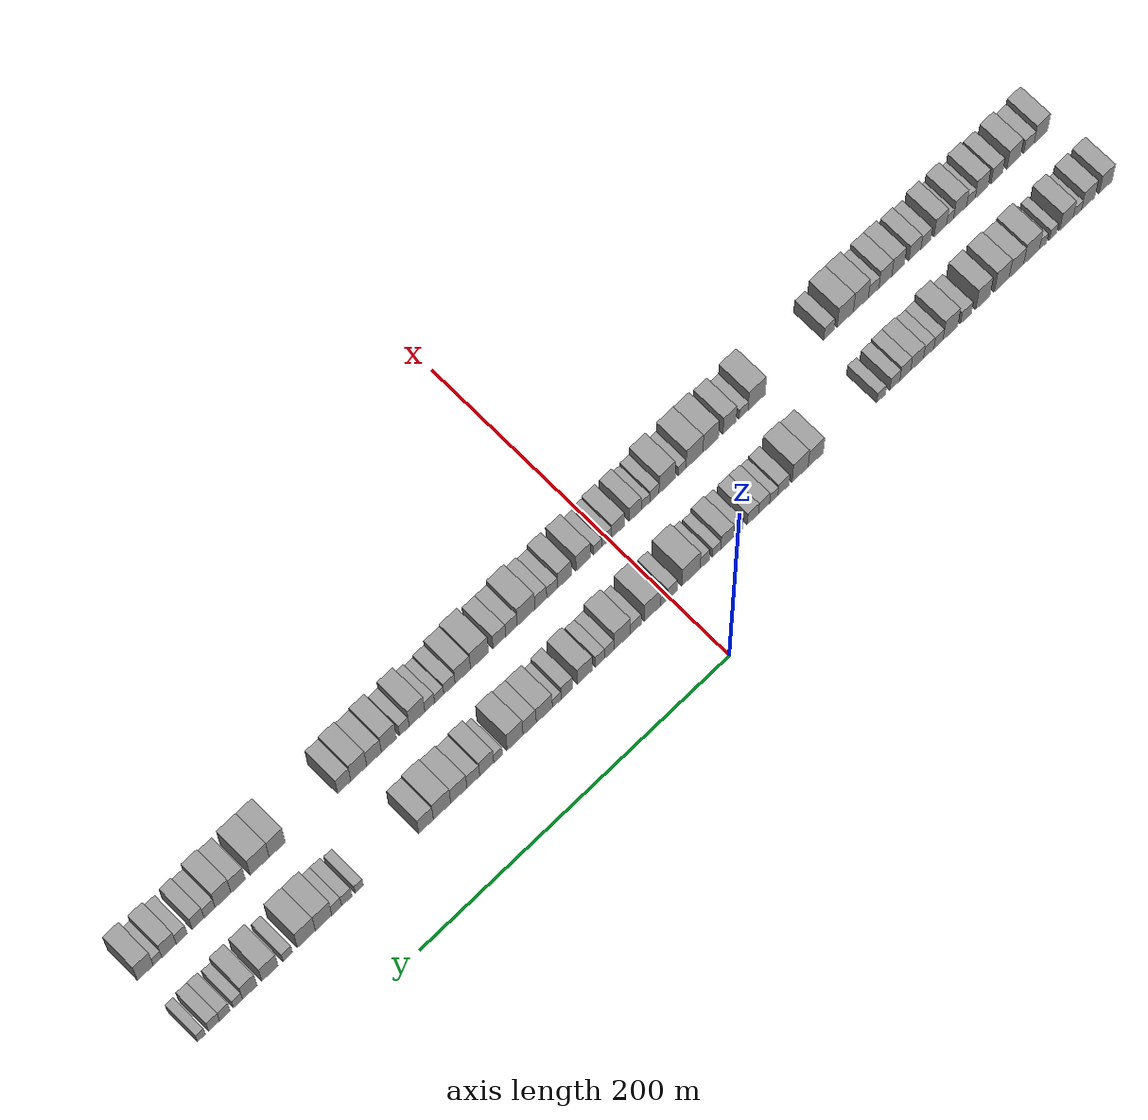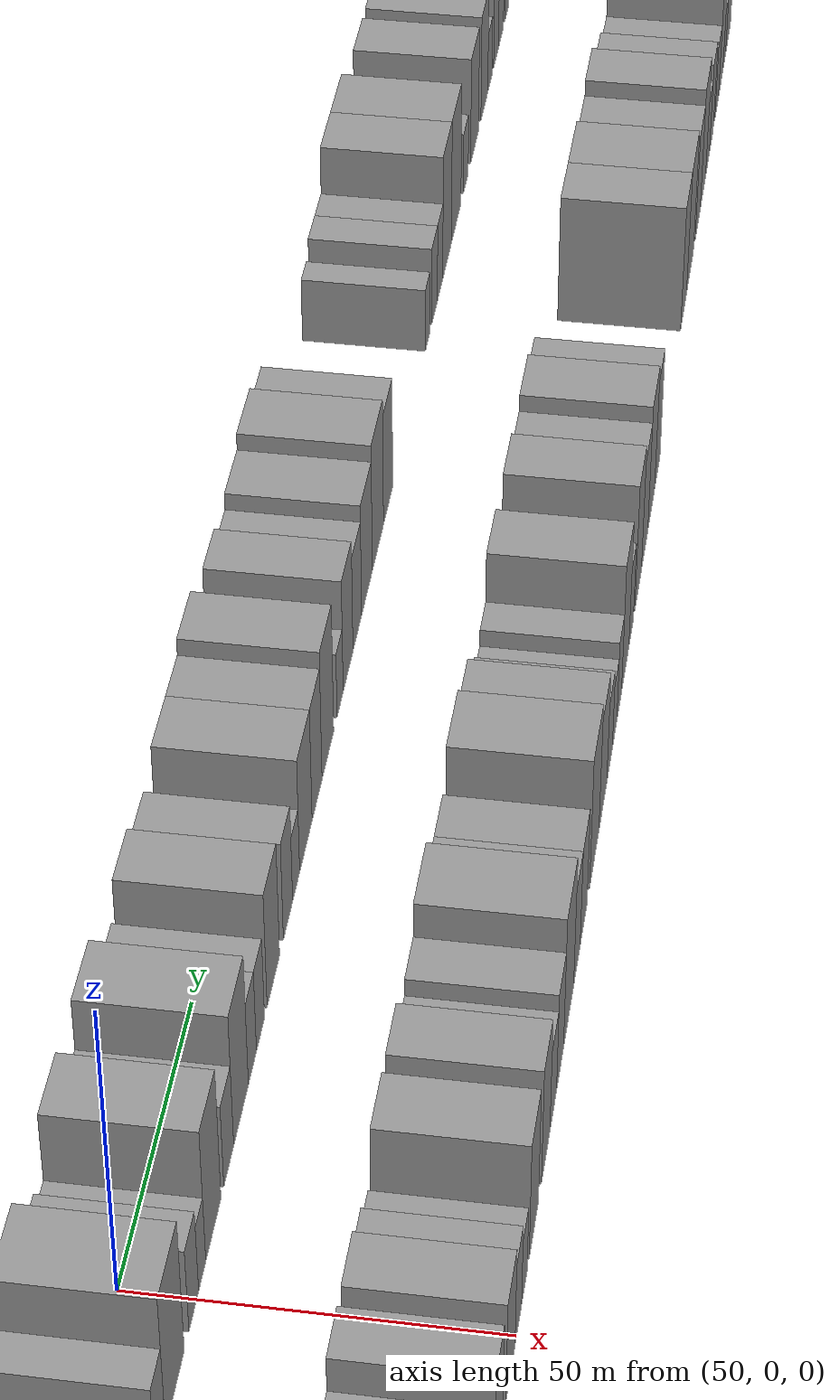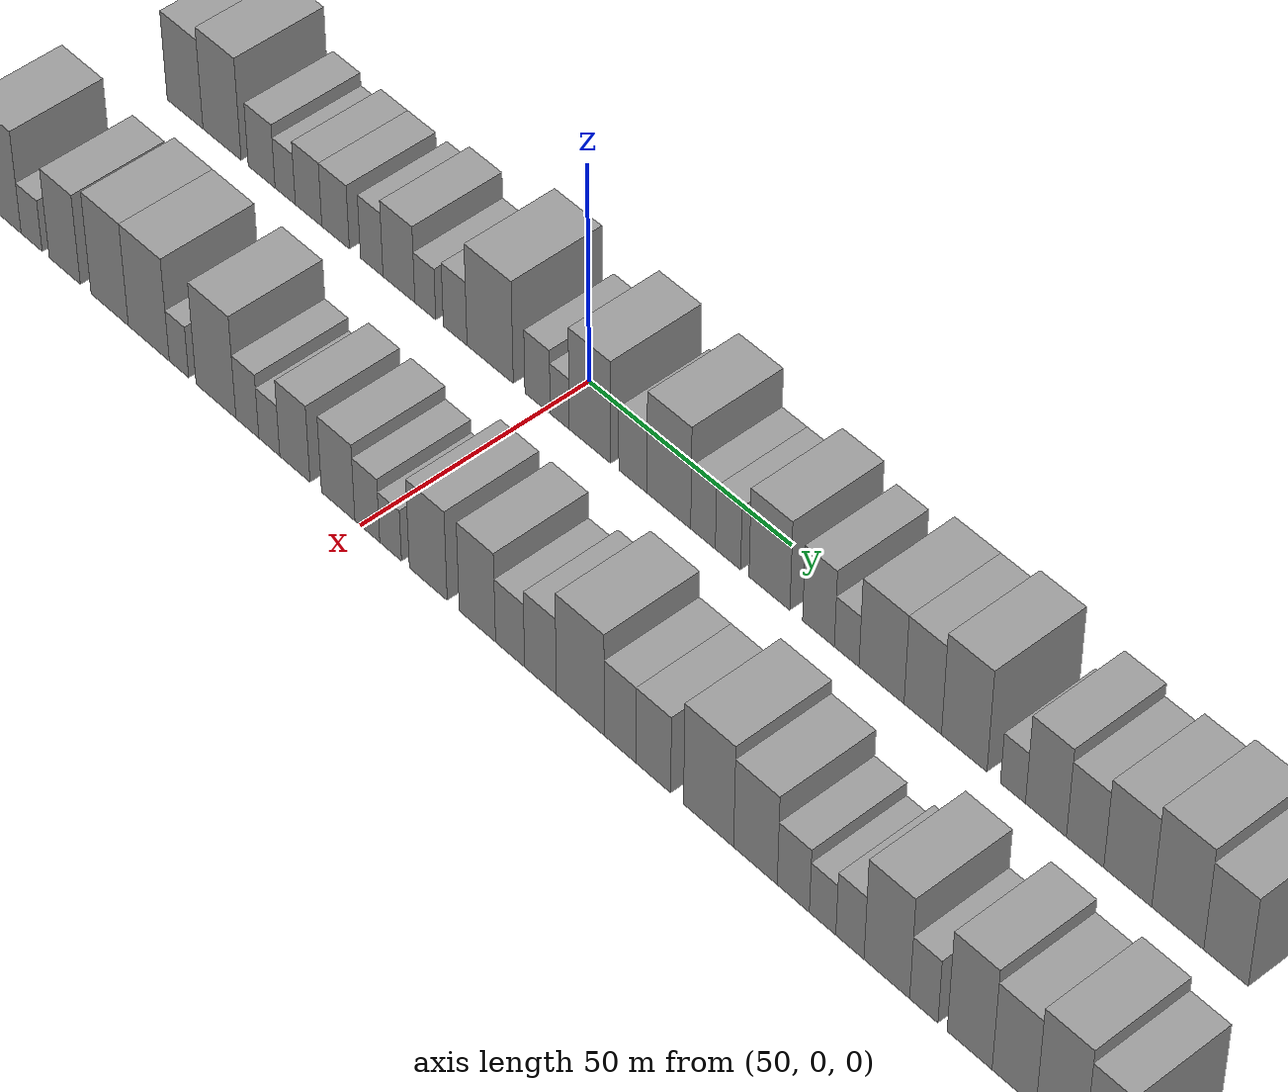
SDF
<sdf version="1.6">
 <world name="default">
  <scene>
   <sky><clouds><speed>12</speed></clouds></sky>
   <ambient>0.4 0.4 0.4 1</ambient>
   <background>0.7 0.7 0.7 1</background>
   <shadows>1</shadows>
  </scene>
  <gravity>0 0 -9.8066</gravity>
  <magnetic_field>6e-06 2.3e-05 -4.2e-05</magnetic_field>
  <physics default="0" name="default_physics" type="ode">
   <ode>
    <solver>
     <type>quick</type>
     <iters>10</iters>
     <sor>1.0</sor>
     <use_dynamic_moi_rescaling>0</use_dynamic_moi_rescaling>
    </solver>
    <constraints>
     <cfm>0</cfm>
     <erp>0.2</erp>
     <contact_max_correcting_vel>100</contact_max_correcting_vel>
     <contact_surface_layer>0.001</contact_surface_layer>
    </constraints>
   </ode>
   <max_step_size>0.004</max_step_size>
   <real_time_factor>1</real_time_factor>
   <real_time_update_rate>250</real_time_update_rate>
  </physics>
  <light name="sun" type="directional">
   <pose>0 0 10 0 0 0</pose>
   <diffuse>0.8 0.8 0.8 1</diffuse>
   <specular>0.2 0.2 0.2 1</specular>
   <attenuation>
    <range>1000</range>
    <constant>0.9</constant>
    <linear>0.01</linear>
    <quadratic>0.001</quadratic>
   </attenuation>
   <direction>-0.5 0.1 -0.9</direction>
  </light>
  <model name="building_1">
   <static>1</static>
   <pose>50.0000 -295.5026 0 0.000000 0.000000 0.000000</pose>
   <link name="link">
    <pose>0 0 10.50 0 0 0</pose>
    <collision name="collision"><geometry><box><size>20.0000 8.9949 21.0000</size></box></geometry></collision>
    <visual name="visual">
     <cast_shadows>0</cast_shadows>
     <geometry><box><size>20.0000 8.9949 21.0000</size></box></geometry>
     <material>
      <script>
       <uri>model://grey_wall/materials/scripts</uri>
       <uri>model://grey_wall/materials/textures</uri>
       <name>vrc/grey_wall</name>
      </script>
     </material>
    </visual>
   </link>
  </model>
  <model name="building_2">
   <static>1</static>
   <pose>50.0000 -283.3810 0 0.000000 0.000000 0.000000</pose>
   <link name="link">
    <pose>0 0 10.50 0 0 0</pose>
    <collision name="collision"><geometry><box><size>20.0000 9.2483 21.0000</size></box></geometry></collision>
    <visual name="visual">
     <cast_shadows>0</cast_shadows>
     <geometry><box><size>20.0000 9.2483 21.0000</size></box></geometry>
     <material>
      <script>
       <uri>model://grey_wall/materials/scripts</uri>
       <uri>model://grey_wall/materials/textures</uri>
       <name>vrc/grey_wall</name>
      </script>
     </material>
    </visual>
   </link>
  </model>
  <model name="building_3">
   <static>1</static>
   <pose>50.0000 -275.8437 0 0.000000 0.000000 0.000000</pose>
   <link name="link">
    <pose>0 0 6.00 0 0 0</pose>
    <collision name="collision"><geometry><box><size>20.0000 5.8264 12.0000</size></box></geometry></collision>
    <visual name="visual">
     <cast_shadows>0</cast_shadows>
     <geometry><box><size>20.0000 5.8264 12.0000</size></box></geometry>
     <material>
      <script>
       <uri>model://grey_wall/materials/scripts</uri>
       <uri>model://grey_wall/materials/textures</uri>
       <name>vrc/grey_wall</name>
      </script>
     </material>
    </visual>
   </link>
  </model>
  <model name="building_4">
   <static>1</static>
   <pose>50.0000 -268.2527 0 0.000000 0.000000 0.000000</pose>
   <link name="link">
    <pose>0 0 10.50 0 0 0</pose>
    <collision name="collision"><geometry><box><size>20.0000 9.3556 21.0000</size></box></geometry></collision>
    <visual name="visual">
     <cast_shadows>0</cast_shadows>
     <geometry><box><size>20.0000 9.3556 21.0000</size></box></geometry>
     <material>
      <script>
       <uri>model://grey_wall/materials/scripts</uri>
       <uri>model://grey_wall/materials/textures</uri>
       <name>vrc/grey_wall</name>
      </script>
     </material>
    </visual>
   </link>
  </model>
  <model name="building_5">
   <static>1</static>
   <pose>50.0000 -259.0420 0 0.000000 0.000000 0.000000</pose>
   <link name="link">
    <pose>0 0 6.00 0 0 0</pose>
    <collision name="collision"><geometry><box><size>20.0000 5.0658 12.0000</size></box></geometry></collision>
    <visual name="visual">
     <cast_shadows>0</cast_shadows>
     <geometry><box><size>20.0000 5.0658 12.0000</size></box></geometry>
     <material>
      <script>
       <uri>model://grey_wall/materials/scripts</uri>
       <uri>model://grey_wall/materials/textures</uri>
       <name>vrc/grey_wall</name>
      </script>
     </material>
    </visual>
   </link>
  </model>
  <model name="building_6">
   <static>1</static>
   <pose>50.0000 -251.9958 0 0.000000 0.000000 0.000000</pose>
   <link name="link">
    <pose>0 0 6.00 0 0 0</pose>
    <collision name="collision"><geometry><box><size>20.0000 5.0266 12.0000</size></box></geometry></collision>
    <visual name="visual">
     <cast_shadows>0</cast_shadows>
     <geometry><box><size>20.0000 5.0266 12.0000</size></box></geometry>
     <material>
      <script>
       <uri>model://grey_wall/materials/scripts</uri>
       <uri>model://grey_wall/materials/textures</uri>
       <name>vrc/grey_wall</name>
      </script>
     </material>
    </visual>
   </link>
  </model>
  <model name="building_7">
   <static>1</static>
   <pose>50.0000 -244.0450 0 0.000000 0.000000 0.000000</pose>
   <link name="link">
    <pose>0 0 12.00 0 0 0</pose>
    <collision name="collision"><geometry><box><size>20.0000 10.8750 24.0000</size></box></geometry></collision>
    <visual name="visual">
     <cast_shadows>0</cast_shadows>
     <geometry><box><size>20.0000 10.8750 24.0000</size></box></geometry>
     <material>
      <script>
       <uri>model://grey_wall/materials/scripts</uri>
       <uri>model://grey_wall/materials/textures</uri>
       <name>vrc/grey_wall</name>
      </script>
     </material>
    </visual>
   </link>
  </model>
  <model name="building_8">
   <static>1</static>
   <pose>50.0000 -233.6222 0 0.000000 0.000000 0.000000</pose>
   <link name="link">
    <pose>0 0 10.50 0 0 0</pose>
    <collision name="collision"><geometry><box><size>20.0000 9.9707 21.0000</size></box></geometry></collision>
    <visual name="visual">
     <cast_shadows>0</cast_shadows>
     <geometry><box><size>20.0000 9.9707 21.0000</size></box></geometry>
     <material>
      <script>
       <uri>model://grey_wall/materials/scripts</uri>
       <uri>model://grey_wall/materials/textures</uri>
       <name>vrc/grey_wall</name>
      </script>
     </material>
    </visual>
   </link>
  </model>
  <model name="building_9">
   <static>1</static>
   <pose>50.0000 -223.5442 0 0.000000 0.000000 0.000000</pose>
   <link name="link">
    <pose>0 0 12.00 0 0 0</pose>
    <collision name="collision"><geometry><box><size>20.0000 10.1853 24.0000</size></box></geometry></collision>
    <visual name="visual">
     <cast_shadows>0</cast_shadows>
     <geometry><box><size>20.0000 10.1853 24.0000</size></box></geometry>
     <material>
      <script>
       <uri>model://grey_wall/materials/scripts</uri>
       <uri>model://grey_wall/materials/textures</uri>
       <name>vrc/grey_wall</name>
      </script>
     </material>
    </visual>
   </link>
  </model>
  <model name="building_10">
   <static>1</static>
   <pose>50.0000 -210.5906 0 0.000000 0.000000 0.000000</pose>
   <link name="link">
    <pose>0 0 12.00 0 0 0</pose>
    <collision name="collision"><geometry><box><size>20.0000 9.7218 24.0000</size></box></geometry></collision>
    <visual name="visual">
     <cast_shadows>0</cast_shadows>
     <geometry><box><size>20.0000 9.7218 24.0000</size></box></geometry>
     <material>
      <script>
       <uri>model://grey_wall/materials/scripts</uri>
       <uri>model://grey_wall/materials/textures</uri>
       <name>vrc/grey_wall</name>
      </script>
     </material>
    </visual>
   </link>
  </model>
  <model name="building_11">
   <static>1</static>
   <pose>50.0000 -198.9973 0 0.000000 0.000000 0.000000</pose>
   <link name="link">
    <pose>0 0 7.50 0 0 0</pose>
    <collision name="collision"><geometry><box><size>20.0000 7.4648 15.0000</size></box></geometry></collision>
    <visual name="visual">
     <cast_shadows>0</cast_shadows>
     <geometry><box><size>20.0000 7.4648 15.0000</size></box></geometry>
     <material>
      <script>
       <uri>model://grey_wall/materials/scripts</uri>
       <uri>model://grey_wall/materials/textures</uri>
       <name>vrc/grey_wall</name>
      </script>
     </material>
    </visual>
   </link>
  </model>
  <model name="building_12">
   <static>1</static>
   <pose>50.0000 -188.2195 0 0.000000 0.000000 0.000000</pose>
   <link name="link">
    <pose>0 0 12.00 0 0 0</pose>
    <collision name="collision"><geometry><box><size>20.0000 10.0909 24.0000</size></box></geometry></collision>
    <visual name="visual">
     <cast_shadows>0</cast_shadows>
     <geometry><box><size>20.0000 10.0909 24.0000</size></box></geometry>
     <material>
      <script>
       <uri>model://grey_wall/materials/scripts</uri>
       <uri>model://grey_wall/materials/textures</uri>
       <name>vrc/grey_wall</name>
      </script>
     </material>
    </visual>
   </link>
  </model>
  <model name="building_13">
   <static>1</static>
   <pose>50.0000 -180.0950 0 0.000000 0.000000 0.000000</pose>
   <link name="link">
    <pose>0 0 7.50 0 0 0</pose>
    <collision name="collision"><geometry><box><size>20.0000 6.1581 15.0000</size></box></geometry></collision>
    <visual name="visual">
     <cast_shadows>0</cast_shadows>
     <geometry><box><size>20.0000 6.1581 15.0000</size></box></geometry>
     <material>
      <script>
       <uri>model://grey_wall/materials/scripts</uri>
       <uri>model://grey_wall/materials/textures</uri>
       <name>vrc/grey_wall</name>
      </script>
     </material>
    </visual>
   </link>
  </model>
  <model name="building_14">
   <static>1</static>
   <pose>50.0000 -173.4898 0 0.000000 0.000000 0.000000</pose>
   <link name="link">
    <pose>0 0 7.50 0 0 0</pose>
    <collision name="collision"><geometry><box><size>20.0000 7.0522 15.0000</size></box></geometry></collision>
    <visual name="visual">
     <cast_shadows>0</cast_shadows>
     <geometry><box><size>20.0000 7.0522 15.0000</size></box></geometry>
     <material>
      <script>
       <uri>model://grey_wall/materials/scripts</uri>
       <uri>model://grey_wall/materials/textures</uri>
       <name>vrc/grey_wall</name>
      </script>
     </material>
    </visual>
   </link>
  </model>
  <model name="building_15">
   <static>1</static>
   <pose>50.0000 -165.5544 0 0.000000 0.000000 0.000000</pose>
   <link name="link">
    <pose>0 0 9.00 0 0 0</pose>
    <collision name="collision"><geometry><box><size>20.0000 8.8187 18.0000</size></box></geometry></collision>
    <visual name="visual">
     <cast_shadows>0</cast_shadows>
     <geometry><box><size>20.0000 8.8187 18.0000</size></box></geometry>
     <material>
      <script>
       <uri>model://grey_wall/materials/scripts</uri>
       <uri>model://grey_wall/materials/textures</uri>
       <name>vrc/grey_wall</name>
      </script>
     </material>
    </visual>
   </link>
  </model>
  <model name="building_16">
   <static>1</static>
   <pose>50.0000 -157.5196 0 0.000000 0.000000 0.000000</pose>
   <link name="link">
    <pose>0 0 9.00 0 0 0</pose>
    <collision name="collision"><geometry><box><size>20.0000 7.2508 18.0000</size></box></geometry></collision>
    <visual name="visual">
     <cast_shadows>0</cast_shadows>
     <geometry><box><size>20.0000 7.2508 18.0000</size></box></geometry>
     <material>
      <script>
       <uri>model://grey_wall/materials/scripts</uri>
       <uri>model://grey_wall/materials/textures</uri>
       <name>vrc/grey_wall</name>
      </script>
     </material>
    </visual>
   </link>
  </model>
  <model name="building_17">
   <static>1</static>
   <pose>50.0000 -150.5241 0 0.000000 0.000000 0.000000</pose>
   <link name="link">
    <pose>0 0 7.50 0 0 0</pose>
    <collision name="collision"><geometry><box><size>20.0000 6.7403 15.0000</size></box></geometry></collision>
    <visual name="visual">
     <cast_shadows>0</cast_shadows>
     <geometry><box><size>20.0000 6.7403 15.0000</size></box></geometry>
     <material>
      <script>
       <uri>model://grey_wall/materials/scripts</uri>
       <uri>model://grey_wall/materials/textures</uri>
       <name>vrc/grey_wall</name>
      </script>
     </material>
    </visual>
   </link>
  </model>
  <model name="building_18">
   <static>1</static>
   <pose>50.0000 -141.2317 0 0.000000 0.000000 0.000000</pose>
   <link name="link">
    <pose>0 0 6.00 0 0 0</pose>
    <collision name="collision"><geometry><box><size>20.0000 5.8443 12.0000</size></box></geometry></collision>
    <visual name="visual">
     <cast_shadows>0</cast_shadows>
     <geometry><box><size>20.0000 5.8443 12.0000</size></box></geometry>
     <material>
      <script>
       <uri>model://grey_wall/materials/scripts</uri>
       <uri>model://grey_wall/materials/textures</uri>
       <name>vrc/grey_wall</name>
      </script>
     </material>
    </visual>
   </link>
  </model>
  <model name="building_19">
   <static>1</static>
   <pose>50.0000 -97.0741 0 0.000000 0.000000 0.000000</pose>
   <link name="link">
    <pose>0 0 10.50 0 0 0</pose>
    <collision name="collision"><geometry><box><size>20.0000 10.1570 21.0000</size></box></geometry></collision>
    <visual name="visual">
     <cast_shadows>0</cast_shadows>
     <geometry><box><size>20.0000 10.1570 21.0000</size></box></geometry>
     <material>
      <script>
       <uri>model://grey_wall/materials/scripts</uri>
       <uri>model://grey_wall/materials/textures</uri>
       <name>vrc/grey_wall</name>
      </script>
     </material>
    </visual>
   </link>
  </model>
  <model name="building_20">
   <static>1</static>
   <pose>50.0000 -86.6229 0 0.000000 0.000000 0.000000</pose>
   <link name="link">
    <pose>0 0 12.00 0 0 0</pose>
    <collision name="collision"><geometry><box><size>20.0000 10.7454 24.0000</size></box></geometry></collision>
    <visual name="visual">
     <cast_shadows>0</cast_shadows>
     <geometry><box><size>20.0000 10.7454 24.0000</size></box></geometry>
     <material>
      <script>
       <uri>model://grey_wall/materials/scripts</uri>
       <uri>model://grey_wall/materials/textures</uri>
       <name>vrc/grey_wall</name>
      </script>
     </material>
    </visual>
   </link>
  </model>
  <model name="building_21">
   <static>1</static>
   <pose>50.0000 -75.5183 0 0.000000 0.000000 0.000000</pose>
   <link name="link">
    <pose>0 0 7.50 0 0 0</pose>
    <collision name="collision"><geometry><box><size>20.0000 7.4639 15.0000</size></box></geometry></collision>
    <visual name="visual">
     <cast_shadows>0</cast_shadows>
     <geometry><box><size>20.0000 7.4639 15.0000</size></box></geometry>
     <material>
      <script>
       <uri>model://grey_wall/materials/scripts</uri>
       <uri>model://grey_wall/materials/textures</uri>
       <name>vrc/grey_wall</name>
      </script>
     </material>
    </visual>
   </link>
  </model>
  <model name="building_22">
   <static>1</static>
   <pose>50.0000 -68.9887 0 0.000000 0.000000 0.000000</pose>
   <link name="link">
    <pose>0 0 6.00 0 0 0</pose>
    <collision name="collision"><geometry><box><size>20.0000 5.5952 12.0000</size></box></geometry></collision>
    <visual name="visual">
     <cast_shadows>0</cast_shadows>
     <geometry><box><size>20.0000 5.5952 12.0000</size></box></geometry>
     <material>
      <script>
       <uri>model://grey_wall/materials/scripts</uri>
       <uri>model://grey_wall/materials/textures</uri>
       <name>vrc/grey_wall</name>
      </script>
     </material>
    </visual>
   </link>
  </model>
  <model name="building_23">
   <static>1</static>
   <pose>50.0000 -62.5589 0 0.000000 0.000000 0.000000</pose>
   <link name="link">
    <pose>0 0 7.50 0 0 0</pose>
    <collision name="collision"><geometry><box><size>20.0000 7.2644 15.0000</size></box></geometry></collision>
    <visual name="visual">
     <cast_shadows>0</cast_shadows>
     <geometry><box><size>20.0000 7.2644 15.0000</size></box></geometry>
     <material>
      <script>
       <uri>model://grey_wall/materials/scripts</uri>
       <uri>model://grey_wall/materials/textures</uri>
       <name>vrc/grey_wall</name>
      </script>
     </material>
    </visual>
   </link>
  </model>
  <model name="building_24">
   <static>1</static>
   <pose>50.0000 -55.1906 0 0.000000 0.000000 0.000000</pose>
   <link name="link">
    <pose>0 0 7.50 0 0 0</pose>
    <collision name="collision"><geometry><box><size>20.0000 7.4722 15.0000</size></box></geometry></collision>
    <visual name="visual">
     <cast_shadows>0</cast_shadows>
     <geometry><box><size>20.0000 7.4722 15.0000</size></box></geometry>
     <material>
      <script>
       <uri>model://grey_wall/materials/scripts</uri>
       <uri>model://grey_wall/materials/textures</uri>
       <name>vrc/grey_wall</name>
      </script>
     </material>
    </visual>
   </link>
  </model>
  <model name="building_25">
   <static>1</static>
   <pose>50.0000 -45.4185 0 0.000000 0.000000 0.000000</pose>
   <link name="link">
    <pose>0 0 7.50 0 0 0</pose>
    <collision name="collision"><geometry><box><size>20.0000 6.0720 15.0000</size></box></geometry></collision>
    <visual name="visual">
     <cast_shadows>0</cast_shadows>
     <geometry><box><size>20.0000 6.0720 15.0000</size></box></geometry>
     <material>
      <script>
       <uri>model://grey_wall/materials/scripts</uri>
       <uri>model://grey_wall/materials/textures</uri>
       <name>vrc/grey_wall</name>
      </script>
     </material>
    </visual>
   </link>
  </model>
  <model name="building_26">
   <static>1</static>
   <pose>50.0000 -38.1302 0 0.000000 0.000000 0.000000</pose>
   <link name="link">
    <pose>0 0 9.00 0 0 0</pose>
    <collision name="collision"><geometry><box><size>20.0000 8.5045 18.0000</size></box></geometry></collision>
    <visual name="visual">
     <cast_shadows>0</cast_shadows>
     <geometry><box><size>20.0000 8.5045 18.0000</size></box></geometry>
     <material>
      <script>
       <uri>model://grey_wall/materials/scripts</uri>
       <uri>model://grey_wall/materials/textures</uri>
       <name>vrc/grey_wall</name>
      </script>
     </material>
    </visual>
   </link>
  </model>
  <model name="building_27">
   <static>1</static>
   <pose>50.0000 -31.1226 0 0.000000 0.000000 0.000000</pose>
   <link name="link">
    <pose>0 0 6.00 0 0 0</pose>
    <collision name="collision"><geometry><box><size>20.0000 5.5108 12.0000</size></box></geometry></collision>
    <visual name="visual">
     <cast_shadows>0</cast_shadows>
     <geometry><box><size>20.0000 5.5108 12.0000</size></box></geometry>
     <material>
      <script>
       <uri>model://grey_wall/materials/scripts</uri>
       <uri>model://grey_wall/materials/textures</uri>
       <name>vrc/grey_wall</name>
      </script>
     </material>
    </visual>
   </link>
  </model>
  <model name="building_28">
   <static>1</static>
   <pose>50.0000 -23.2598 0 0.000000 0.000000 0.000000</pose>
   <link name="link">
    <pose>0 0 7.50 0 0 0</pose>
    <collision name="collision"><geometry><box><size>20.0000 6.2147 15.0000</size></box></geometry></collision>
    <visual name="visual">
     <cast_shadows>0</cast_shadows>
     <geometry><box><size>20.0000 6.2147 15.0000</size></box></geometry>
     <material>
      <script>
       <uri>model://grey_wall/materials/scripts</uri>
       <uri>model://grey_wall/materials/textures</uri>
       <name>vrc/grey_wall</name>
      </script>
     </material>
    </visual>
   </link>
  </model>
  <model name="building_29">
   <static>1</static>
   <pose>50.0000 -14.1580 0 0.000000 0.000000 0.000000</pose>
   <link name="link">
    <pose>0 0 12.00 0 0 0</pose>
    <collision name="collision"><geometry><box><size>20.0000 11.9890 24.0000</size></box></geometry></collision>
    <visual name="visual">
     <cast_shadows>0</cast_shadows>
     <geometry><box><size>20.0000 11.9890 24.0000</size></box></geometry>
     <material>
      <script>
       <uri>model://grey_wall/materials/scripts</uri>
       <uri>model://grey_wall/materials/textures</uri>
       <name>vrc/grey_wall</name>
      </script>
     </material>
    </visual>
   </link>
  </model>
  <model name="building_30">
   <static>1</static>
   <pose>50.0000 -1.9397 0 0.000000 0.000000 0.000000</pose>
   <link name="link">
    <pose>0 0 7.50 0 0 0</pose>
    <collision name="collision"><geometry><box><size>20.0000 6.4475 15.0000</size></box></geometry></collision>
    <visual name="visual">
     <cast_shadows>0</cast_shadows>
     <geometry><box><size>20.0000 6.4475 15.0000</size></box></geometry>
     <material>
      <script>
       <uri>model://grey_wall/materials/scripts</uri>
       <uri>model://grey_wall/materials/textures</uri>
       <name>vrc/grey_wall</name>
      </script>
     </material>
    </visual>
   </link>
  </model>
  <model name="building_31">
   <static>1</static>
   <pose>50.0000 3.7047 0 0.000000 0.000000 0.000000</pose>
   <link name="link">
    <pose>0 0 6.00 0 0 0</pose>
    <collision name="collision"><geometry><box><size>20.0000 4.8413 12.0000</size></box></geometry></collision>
    <visual name="visual">
     <cast_shadows>0</cast_shadows>
     <geometry><box><size>20.0000 4.8413 12.0000</size></box></geometry>
     <material>
      <script>
       <uri>model://grey_wall/materials/scripts</uri>
       <uri>model://grey_wall/materials/textures</uri>
       <name>vrc/grey_wall</name>
      </script>
     </material>
    </visual>
   </link>
  </model>
  <model name="building_32">
   <static>1</static>
   <pose>50.0000 11.3556 0 0.000000 0.000000 0.000000</pose>
   <link name="link">
    <pose>0 0 12.00 0 0 0</pose>
    <collision name="collision"><geometry><box><size>20.0000 10.4605 24.0000</size></box></geometry></collision>
    <visual name="visual">
     <cast_shadows>0</cast_shadows>
     <geometry><box><size>20.0000 10.4605 24.0000</size></box></geometry>
     <material>
      <script>
       <uri>model://grey_wall/materials/scripts</uri>
       <uri>model://grey_wall/materials/textures</uri>
       <name>vrc/grey_wall</name>
      </script>
     </material>
    </visual>
   </link>
  </model>
  <model name="building_33">
   <static>1</static>
   <pose>50.0000 22.0970 0 0.000000 0.000000 0.000000</pose>
   <link name="link">
    <pose>0 0 7.50 0 0 0</pose>
    <collision name="collision"><geometry><box><size>20.0000 7.0223 15.0000</size></box></geometry></collision>
    <visual name="visual">
     <cast_shadows>0</cast_shadows>
     <geometry><box><size>20.0000 7.0223 15.0000</size></box></geometry>
     <material>
      <script>
       <uri>model://grey_wall/materials/scripts</uri>
       <uri>model://grey_wall/materials/textures</uri>
       <name>vrc/grey_wall</name>
      </script>
     </material>
    </visual>
   </link>
  </model>
  <model name="building_34">
   <static>1</static>
   <pose>50.0000 30.9738 0 0.000000 0.000000 0.000000</pose>
   <link name="link">
    <pose>0 0 12.00 0 0 0</pose>
    <collision name="collision"><geometry><box><size>20.0000 10.7313 24.0000</size></box></geometry></collision>
    <visual name="visual">
     <cast_shadows>0</cast_shadows>
     <geometry><box><size>20.0000 10.7313 24.0000</size></box></geometry>
     <material>
      <script>
       <uri>model://grey_wall/materials/scripts</uri>
       <uri>model://grey_wall/materials/textures</uri>
       <name>vrc/grey_wall</name>
      </script>
     </material>
    </visual>
   </link>
  </model>
  <model name="building_35">
   <static>1</static>
   <pose>50.0000 39.3434 0 0.000000 0.000000 0.000000</pose>
   <link name="link">
    <pose>0 0 7.50 0 0 0</pose>
    <collision name="collision"><geometry><box><size>20.0000 6.0079 15.0000</size></box></geometry></collision>
    <visual name="visual">
     <cast_shadows>0</cast_shadows>
     <geometry><box><size>20.0000 6.0079 15.0000</size></box></geometry>
     <material>
      <script>
       <uri>model://grey_wall/materials/scripts</uri>
       <uri>model://grey_wall/materials/textures</uri>
       <name>vrc/grey_wall</name>
      </script>
     </material>
    </visual>
   </link>
  </model>
  <model name="building_36">
   <static>1</static>
   <pose>50.0000 45.4067 0 0.000000 0.000000 0.000000</pose>
   <link name="link">
    <pose>0 0 7.50 0 0 0</pose>
    <collision name="collision"><geometry><box><size>20.0000 6.1187 15.0000</size></box></geometry></collision>
    <visual name="visual">
     <cast_shadows>0</cast_shadows>
     <geometry><box><size>20.0000 6.1187 15.0000</size></box></geometry>
     <material>
      <script>
       <uri>model://grey_wall/materials/scripts</uri>
       <uri>model://grey_wall/materials/textures</uri>
       <name>vrc/grey_wall</name>
      </script>
     </material>
    </visual>
   </link>
  </model>
  <model name="building_37">
   <static>1</static>
   <pose>50.0000 55.3528 0 0.000000 0.000000 0.000000</pose>
   <link name="link">
    <pose>0 0 10.50 0 0 0</pose>
    <collision name="collision"><geometry><box><size>20.0000 9.7734 21.0000</size></box></geometry></collision>
    <visual name="visual">
     <cast_shadows>0</cast_shadows>
     <geometry><box><size>20.0000 9.7734 21.0000</size></box></geometry>
     <material>
      <script>
       <uri>model://grey_wall/materials/scripts</uri>
       <uri>model://grey_wall/materials/textures</uri>
       <name>vrc/grey_wall</name>
      </script>
     </material>
    </visual>
   </link>
  </model>
  <model name="building_38">
   <static>1</static>
   <pose>50.0000 66.9784 0 0.000000 0.000000 0.000000</pose>
   <link name="link">
    <pose>0 0 9.00 0 0 0</pose>
    <collision name="collision"><geometry><box><size>20.0000 7.4777 18.0000</size></box></geometry></collision>
    <visual name="visual">
     <cast_shadows>0</cast_shadows>
     <geometry><box><size>20.0000 7.4777 18.0000</size></box></geometry>
     <material>
      <script>
       <uri>model://grey_wall/materials/scripts</uri>
       <uri>model://grey_wall/materials/textures</uri>
       <name>vrc/grey_wall</name>
      </script>
     </material>
    </visual>
   </link>
  </model>
  <model name="building_39">
   <static>1</static>
   <pose>50.0000 73.5964 0 0.000000 0.000000 0.000000</pose>
   <link name="link">
    <pose>0 0 6.00 0 0 0</pose>
    <collision name="collision"><geometry><box><size>20.0000 5.7583 12.0000</size></box></geometry></collision>
    <visual name="visual">
     <cast_shadows>0</cast_shadows>
     <geometry><box><size>20.0000 5.7583 12.0000</size></box></geometry>
     <material>
      <script>
       <uri>model://grey_wall/materials/scripts</uri>
       <uri>model://grey_wall/materials/textures</uri>
       <name>vrc/grey_wall</name>
      </script>
     </material>
    </visual>
   </link>
  </model>
  <model name="building_40">
   <static>1</static>
   <pose>50.0000 81.6918 0 0.000000 0.000000 0.000000</pose>
   <link name="link">
    <pose>0 0 10.50 0 0 0</pose>
    <collision name="collision"><geometry><box><size>20.0000 10.4326 21.0000</size></box></geometry></collision>
    <visual name="visual">
     <cast_shadows>0</cast_shadows>
     <geometry><box><size>20.0000 10.4326 21.0000</size></box></geometry>
     <material>
      <script>
       <uri>model://grey_wall/materials/scripts</uri>
       <uri>model://grey_wall/materials/textures</uri>
       <name>vrc/grey_wall</name>
      </script>
     </material>
    </visual>
   </link>
  </model>
  <model name="building_41">
   <static>1</static>
   <pose>50.0000 91.1878 0 0.000000 0.000000 0.000000</pose>
   <link name="link">
    <pose>0 0 10.50 0 0 0</pose>
    <collision name="collision"><geometry><box><size>20.0000 8.5594 21.0000</size></box></geometry></collision>
    <visual name="visual">
     <cast_shadows>0</cast_shadows>
     <geometry><box><size>20.0000 8.5594 21.0000</size></box></geometry>
     <material>
      <script>
       <uri>model://grey_wall/materials/scripts</uri>
       <uri>model://grey_wall/materials/textures</uri>
       <name>vrc/grey_wall</name>
      </script>
     </material>
    </visual>
   </link>
  </model>
  <model name="building_42">
   <static>1</static>
   <pose>50.0000 100.6105 0 0.000000 0.000000 0.000000</pose>
   <link name="link">
    <pose>0 0 12.00 0 0 0</pose>
    <collision name="collision"><geometry><box><size>20.0000 10.2859 24.0000</size></box></geometry></collision>
    <visual name="visual">
     <cast_shadows>0</cast_shadows>
     <geometry><box><size>20.0000 10.2859 24.0000</size></box></geometry>
     <material>
      <script>
       <uri>model://grey_wall/materials/scripts</uri>
       <uri>model://grey_wall/materials/textures</uri>
       <name>vrc/grey_wall</name>
      </script>
     </material>
    </visual>
   </link>
  </model>
  <model name="building_43">
   <static>1</static>
   <pose>50.0000 111.5396 0 0.000000 0.000000 0.000000</pose>
   <link name="link">
    <pose>0 0 6.00 0 0 0</pose>
    <collision name="collision"><geometry><box><size>20.0000 5.5724 12.0000</size></box></geometry></collision>
    <visual name="visual">
     <cast_shadows>0</cast_shadows>
     <geometry><box><size>20.0000 5.5724 12.0000</size></box></geometry>
     <material>
      <script>
       <uri>model://grey_wall/materials/scripts</uri>
       <uri>model://grey_wall/materials/textures</uri>
       <name>vrc/grey_wall</name>
      </script>
     </material>
    </visual>
   </link>
  </model>
  <model name="building_44">
   <static>1</static>
   <pose>50.0000 118.8459 0 0.000000 0.000000 0.000000</pose>
   <link name="link">
    <pose>0 0 10.50 0 0 0</pose>
    <collision name="collision"><geometry><box><size>20.0000 9.0402 21.0000</size></box></geometry></collision>
    <visual name="visual">
     <cast_shadows>0</cast_shadows>
     <geometry><box><size>20.0000 9.0402 21.0000</size></box></geometry>
     <material>
      <script>
       <uri>model://grey_wall/materials/scripts</uri>
       <uri>model://grey_wall/materials/textures</uri>
       <name>vrc/grey_wall</name>
      </script>
     </material>
    </visual>
   </link>
  </model>
  <model name="building_45">
   <static>1</static>
   <pose>50.0000 127.4547 0 0.000000 0.000000 0.000000</pose>
   <link name="link">
    <pose>0 0 9.00 0 0 0</pose>
    <collision name="collision"><geometry><box><size>20.0000 8.1775 18.0000</size></box></geometry></collision>
    <visual name="visual">
     <cast_shadows>0</cast_shadows>
     <geometry><box><size>20.0000 8.1775 18.0000</size></box></geometry>
     <material>
      <script>
       <uri>model://grey_wall/materials/scripts</uri>
       <uri>model://grey_wall/materials/textures</uri>
       <name>vrc/grey_wall</name>
      </script>
     </material>
    </visual>
   </link>
  </model>
  <model name="building_46">
   <static>1</static>
   <pose>50.0000 136.7219 0 0.000000 0.000000 0.000000</pose>
   <link name="link">
    <pose>0 0 10.50 0 0 0</pose>
    <collision name="collision"><geometry><box><size>20.0000 10.3569 21.0000</size></box></geometry></collision>
    <visual name="visual">
     <cast_shadows>0</cast_shadows>
     <geometry><box><size>20.0000 10.3569 21.0000</size></box></geometry>
     <material>
      <script>
       <uri>model://grey_wall/materials/scripts</uri>
       <uri>model://grey_wall/materials/textures</uri>
       <name>vrc/grey_wall</name>
      </script>
     </material>
    </visual>
   </link>
  </model>
  <model name="building_47">
   <static>1</static>
   <pose>50.0000 147.4399 0 0.000000 0.000000 0.000000</pose>
   <link name="link">
    <pose>0 0 12.00 0 0 0</pose>
    <collision name="collision"><geometry><box><size>20.0000 11.0789 24.0000</size></box></geometry></collision>
    <visual name="visual">
     <cast_shadows>0</cast_shadows>
     <geometry><box><size>20.0000 11.0789 24.0000</size></box></geometry>
     <material>
      <script>
       <uri>model://grey_wall/materials/scripts</uri>
       <uri>model://grey_wall/materials/textures</uri>
       <name>vrc/grey_wall</name>
      </script>
     </material>
    </visual>
   </link>
  </model>
  <model name="building_48">
   <static>1</static>
   <pose>50.0000 157.6778 0 0.000000 0.000000 0.000000</pose>
   <link name="link">
    <pose>0 0 10.50 0 0 0</pose>
    <collision name="collision"><geometry><box><size>20.0000 9.3970 21.0000</size></box></geometry></collision>
    <visual name="visual">
     <cast_shadows>0</cast_shadows>
     <geometry><box><size>20.0000 9.3970 21.0000</size></box></geometry>
     <material>
      <script>
       <uri>model://grey_wall/materials/scripts</uri>
       <uri>model://grey_wall/materials/textures</uri>
       <name>vrc/grey_wall</name>
      </script>
     </material>
    </visual>
   </link>
  </model>
  <model name="building_49">
   <static>1</static>
   <pose>50.0000 199.9840 0 0.000000 0.000000 0.000000</pose>
   <link name="link">
    <pose>0 0 6.00 0 0 0</pose>
    <collision name="collision"><geometry><box><size>20.0000 5.0718 12.0000</size></box></geometry></collision>
    <visual name="visual">
     <cast_shadows>0</cast_shadows>
     <geometry><box><size>20.0000 5.0718 12.0000</size></box></geometry>
     <material>
      <script>
       <uri>model://grey_wall/materials/scripts</uri>
       <uri>model://grey_wall/materials/textures</uri>
       <name>vrc/grey_wall</name>
      </script>
     </material>
    </visual>
   </link>
  </model>
  <model name="building_50">
   <static>1</static>
   <pose>50.0000 207.8070 0 0.000000 0.000000 0.000000</pose>
   <link name="link">
    <pose>0 0 7.50 0 0 0</pose>
    <collision name="collision"><geometry><box><size>20.0000 6.5744 15.0000</size></box></geometry></collision>
    <visual name="visual">
     <cast_shadows>0</cast_shadows>
     <geometry><box><size>20.0000 6.5744 15.0000</size></box></geometry>
     <material>
      <script>
       <uri>model://grey_wall/materials/scripts</uri>
       <uri>model://grey_wall/materials/textures</uri>
       <name>vrc/grey_wall</name>
      </script>
     </material>
    </visual>
   </link>
  </model>
  <model name="building_51">
   <static>1</static>
   <pose>50.0000 214.1928 0 0.000000 0.000000 0.000000</pose>
   <link name="link">
    <pose>0 0 7.50 0 0 0</pose>
    <collision name="collision"><geometry><box><size>20.0000 6.1971 15.0000</size></box></geometry></collision>
    <visual name="visual">
     <cast_shadows>0</cast_shadows>
     <geometry><box><size>20.0000 6.1971 15.0000</size></box></geometry>
     <material>
      <script>
       <uri>model://grey_wall/materials/scripts</uri>
       <uri>model://grey_wall/materials/textures</uri>
       <name>vrc/grey_wall</name>
      </script>
     </material>
    </visual>
   </link>
  </model>
  <model name="building_52">
   <static>1</static>
   <pose>50.0000 222.4726 0 0.000000 0.000000 0.000000</pose>
   <link name="link">
    <pose>0 0 12.00 0 0 0</pose>
    <collision name="collision"><geometry><box><size>20.0000 10.3624 24.0000</size></box></geometry></collision>
    <visual name="visual">
     <cast_shadows>0</cast_shadows>
     <geometry><box><size>20.0000 10.3624 24.0000</size></box></geometry>
     <material>
      <script>
       <uri>model://grey_wall/materials/scripts</uri>
       <uri>model://grey_wall/materials/textures</uri>
       <name>vrc/grey_wall</name>
      </script>
     </material>
    </visual>
   </link>
  </model>
  <model name="building_53">
   <static>1</static>
   <pose>50.0000 233.3145 0 0.000000 0.000000 0.000000</pose>
   <link name="link">
    <pose>0 0 12.00 0 0 0</pose>
    <collision name="collision"><geometry><box><size>20.0000 11.3215 24.0000</size></box></geometry></collision>
    <visual name="visual">
     <cast_shadows>0</cast_shadows>
     <geometry><box><size>20.0000 11.3215 24.0000</size></box></geometry>
     <material>
      <script>
       <uri>model://grey_wall/materials/scripts</uri>
       <uri>model://grey_wall/materials/textures</uri>
       <name>vrc/grey_wall</name>
      </script>
     </material>
    </visual>
   </link>
  </model>
  <model name="building_54">
   <static>1</static>
   <pose>50.0000 244.9647 0 0.000000 0.000000 0.000000</pose>
   <link name="link">
    <pose>0 0 6.00 0 0 0</pose>
    <collision name="collision"><geometry><box><size>20.0000 5.9788 12.0000</size></box></geometry></collision>
    <visual name="visual">
     <cast_shadows>0</cast_shadows>
     <geometry><box><size>20.0000 5.9788 12.0000</size></box></geometry>
     <material>
      <script>
       <uri>model://grey_wall/materials/scripts</uri>
       <uri>model://grey_wall/materials/textures</uri>
       <name>vrc/grey_wall</name>
      </script>
     </material>
    </visual>
   </link>
  </model>
  <model name="building_55">
   <static>1</static>
   <pose>50.0000 256.0269 0 0.000000 0.000000 0.000000</pose>
   <link name="link">
    <pose>0 0 10.50 0 0 0</pose>
    <collision name="collision"><geometry><box><size>20.0000 10.1456 21.0000</size></box></geometry></collision>
    <visual name="visual">
     <cast_shadows>0</cast_shadows>
     <geometry><box><size>20.0000 10.1456 21.0000</size></box></geometry>
     <material>
      <script>
       <uri>model://grey_wall/materials/scripts</uri>
       <uri>model://grey_wall/materials/textures</uri>
       <name>vrc/grey_wall</name>
      </script>
     </material>
    </visual>
   </link>
  </model>
  <model name="building_56">
   <static>1</static>
   <pose>50.0000 268.5991 0 0.000000 0.000000 0.000000</pose>
   <link name="link">
    <pose>0 0 10.50 0 0 0</pose>
    <collision name="collision"><geometry><box><size>20.0000 8.9989 21.0000</size></box></geometry></collision>
    <visual name="visual">
     <cast_shadows>0</cast_shadows>
     <geometry><box><size>20.0000 8.9989 21.0000</size></box></geometry>
     <material>
      <script>
       <uri>model://grey_wall/materials/scripts</uri>
       <uri>model://grey_wall/materials/textures</uri>
       <name>vrc/grey_wall</name>
      </script>
     </material>
    </visual>
   </link>
  </model>
  <model name="building_57">
   <static>1</static>
   <pose>50.0000 275.9537 0 0.000000 0.000000 0.000000</pose>
   <link name="link">
    <pose>0 0 6.00 0 0 0</pose>
    <collision name="collision"><geometry><box><size>20.0000 5.7102 12.0000</size></box></geometry></collision>
    <visual name="visual">
     <cast_shadows>0</cast_shadows>
     <geometry><box><size>20.0000 5.7102 12.0000</size></box></geometry>
     <material>
      <script>
       <uri>model://grey_wall/materials/scripts</uri>
       <uri>model://grey_wall/materials/textures</uri>
       <name>vrc/grey_wall</name>
      </script>
     </material>
    </visual>
   </link>
  </model>
  <model name="building_58">
   <static>1</static>
   <pose>50.0000 284.1111 0 0.000000 0.000000 0.000000</pose>
   <link name="link">
    <pose>0 0 7.50 0 0 0</pose>
    <collision name="collision"><geometry><box><size>20.0000 6.6046 15.0000</size></box></geometry></collision>
    <visual name="visual">
     <cast_shadows>0</cast_shadows>
     <geometry><box><size>20.0000 6.6046 15.0000</size></box></geometry>
     <material>
      <script>
       <uri>model://grey_wall/materials/scripts</uri>
       <uri>model://grey_wall/materials/textures</uri>
       <name>vrc/grey_wall</name>
      </script>
     </material>
    </visual>
   </link>
  </model>
  <model name="building_59">
   <static>1</static>
   <pose>50.0000 290.7950 0 0.000000 0.000000 0.000000</pose>
   <link name="link">
    <pose>0 0 7.50 0 0 0</pose>
    <collision name="collision"><geometry><box><size>20.0000 6.7632 15.0000</size></box></geometry></collision>
    <visual name="visual">
     <cast_shadows>0</cast_shadows>
     <geometry><box><size>20.0000 6.7632 15.0000</size></box></geometry>
     <material>
      <script>
       <uri>model://grey_wall/materials/scripts</uri>
       <uri>model://grey_wall/materials/textures</uri>
       <name>vrc/grey_wall</name>
      </script>
     </material>
    </visual>
   </link>
  </model>
  <model name="building_60">
   <static>1</static>
   <pose>50.0000 298.6488 0 0.000000 0.000000 0.000000</pose>
   <link name="link">
    <pose>0 0 6.00 0 0 0</pose>
    <collision name="collision"><geometry><box><size>20.0000 4.9443 12.0000</size></box></geometry></collision>
    <visual name="visual">
     <cast_shadows>0</cast_shadows>
     <geometry><box><size>20.0000 4.9443 12.0000</size></box></geometry>
     <material>
      <script>
       <uri>model://grey_wall/materials/scripts</uri>
       <uri>model://grey_wall/materials/textures</uri>
       <name>vrc/grey_wall</name>
      </script>
     </material>
    </visual>
   </link>
  </model>
  <model name="building_61">
   <static>1</static>
   <pose>90.0000 -292.3551 0 0.000000 0.000000 0.000000</pose>
   <link name="link">
    <pose>0 0 10.50 0 0 0</pose>
    <collision name="collision"><geometry><box><size>20.0000 9.2899 21.0000</size></box></geometry></collision>
    <visual name="visual">
     <cast_shadows>0</cast_shadows>
     <geometry><box><size>20.0000 9.2899 21.0000</size></box></geometry>
     <material>
      <script>
       <uri>model://grey_wall/materials/scripts</uri>
       <uri>model://grey_wall/materials/textures</uri>
       <name>vrc/grey_wall</name>
      </script>
     </material>
    </visual>
   </link>
  </model>
  <model name="building_62">
   <static>1</static>
   <pose>90.0000 -284.0336 0 0.000000 0.000000 0.000000</pose>
   <link name="link">
    <pose>0 0 7.50 0 0 0</pose>
    <collision name="collision"><geometry><box><size>20.0000 7.3530 15.0000</size></box></geometry></collision>
    <visual name="visual">
     <cast_shadows>0</cast_shadows>
     <geometry><box><size>20.0000 7.3530 15.0000</size></box></geometry>
     <material>
      <script>
       <uri>model://grey_wall/materials/scripts</uri>
       <uri>model://grey_wall/materials/textures</uri>
       <name>vrc/grey_wall</name>
      </script>
     </material>
    </visual>
   </link>
  </model>
  <model name="building_63">
   <static>1</static>
   <pose>90.0000 -273.5886 0 0.000000 0.000000 0.000000</pose>
   <link name="link">
    <pose>0 0 10.50 0 0 0</pose>
    <collision name="collision"><geometry><box><size>20.0000 9.5371 21.0000</size></box></geometry></collision>
    <visual name="visual">
     <cast_shadows>0</cast_shadows>
     <geometry><box><size>20.0000 9.5371 21.0000</size></box></geometry>
     <material>
      <script>
       <uri>model://grey_wall/materials/scripts</uri>
       <uri>model://grey_wall/materials/textures</uri>
       <name>vrc/grey_wall</name>
      </script>
     </material>
    </visual>
   </link>
  </model>
  <model name="building_64">
   <static>1</static>
   <pose>90.0000 -261.7767 0 0.000000 0.000000 0.000000</pose>
   <link name="link">
    <pose>0 0 9.00 0 0 0</pose>
    <collision name="collision"><geometry><box><size>20.0000 8.0865 18.0000</size></box></geometry></collision>
    <visual name="visual">
     <cast_shadows>0</cast_shadows>
     <geometry><box><size>20.0000 8.0865 18.0000</size></box></geometry>
     <material>
      <script>
       <uri>model://grey_wall/materials/scripts</uri>
       <uri>model://grey_wall/materials/textures</uri>
       <name>vrc/grey_wall</name>
      </script>
     </material>
    </visual>
   </link>
  </model>
  <model name="building_65">
   <static>1</static>
   <pose>90.0000 -251.2065 0 0.000000 0.000000 0.000000</pose>
   <link name="link">
    <pose>0 0 10.50 0 0 0</pose>
    <collision name="collision"><geometry><box><size>20.0000 9.0539 21.0000</size></box></geometry></collision>
    <visual name="visual">
     <cast_shadows>0</cast_shadows>
     <geometry><box><size>20.0000 9.0539 21.0000</size></box></geometry>
     <material>
      <script>
       <uri>model://grey_wall/materials/scripts</uri>
       <uri>model://grey_wall/materials/textures</uri>
       <name>vrc/grey_wall</name>
      </script>
     </material>
    </visual>
   </link>
  </model>
  <model name="building_66">
   <static>1</static>
   <pose>90.0000 -243.7180 0 0.000000 0.000000 0.000000</pose>
   <link name="link">
    <pose>0 0 6.00 0 0 0</pose>
    <collision name="collision"><geometry><box><size>20.0000 5.9230 12.0000</size></box></geometry></collision>
    <visual name="visual">
     <cast_shadows>0</cast_shadows>
     <geometry><box><size>20.0000 5.9230 12.0000</size></box></geometry>
     <material>
      <script>
       <uri>model://grey_wall/materials/scripts</uri>
       <uri>model://grey_wall/materials/textures</uri>
       <name>vrc/grey_wall</name>
      </script>
     </material>
    </visual>
   </link>
  </model>
  <model name="building_67">
   <static>1</static>
   <pose>90.0000 -236.2722 0 0.000000 0.000000 0.000000</pose>
   <link name="link">
    <pose>0 0 10.50 0 0 0</pose>
    <collision name="collision"><geometry><box><size>20.0000 8.9688 21.0000</size></box></geometry></collision>
    <visual name="visual">
     <cast_shadows>0</cast_shadows>
     <geometry><box><size>20.0000 8.9688 21.0000</size></box></geometry>
     <material>
      <script>
       <uri>model://grey_wall/materials/scripts</uri>
       <uri>model://grey_wall/materials/textures</uri>
       <name>vrc/grey_wall</name>
      </script>
     </material>
    </visual>
   </link>
  </model>
  <model name="building_68">
   <static>1</static>
   <pose>90.0000 -229.3848 0 0.000000 0.000000 0.000000</pose>
   <link name="link">
    <pose>0 0 6.00 0 0 0</pose>
    <collision name="collision"><geometry><box><size>20.0000 4.8060 12.0000</size></box></geometry></collision>
    <visual name="visual">
     <cast_shadows>0</cast_shadows>
     <geometry><box><size>20.0000 4.8060 12.0000</size></box></geometry>
     <material>
      <script>
       <uri>model://grey_wall/materials/scripts</uri>
       <uri>model://grey_wall/materials/textures</uri>
       <name>vrc/grey_wall</name>
      </script>
     </material>
    </visual>
   </link>
  </model>
  <model name="building_69">
   <static>1</static>
   <pose>90.0000 -222.6637 0 0.000000 0.000000 0.000000</pose>
   <link name="link">
    <pose>0 0 10.50 0 0 0</pose>
    <collision name="collision"><geometry><box><size>20.0000 8.6363 21.0000</size></box></geometry></collision>
    <visual name="visual">
     <cast_shadows>0</cast_shadows>
     <geometry><box><size>20.0000 8.6363 21.0000</size></box></geometry>
     <material>
      <script>
       <uri>model://grey_wall/materials/scripts</uri>
       <uri>model://grey_wall/materials/textures</uri>
       <name>vrc/grey_wall</name>
      </script>
     </material>
    </visual>
   </link>
  </model>
  <model name="building_70">
   <static>1</static>
   <pose>90.0000 -212.8325 0 0.000000 0.000000 0.000000</pose>
   <link name="link">
    <pose>0 0 7.50 0 0 0</pose>
    <collision name="collision"><geometry><box><size>20.0000 7.0260 15.0000</size></box></geometry></collision>
    <visual name="visual">
     <cast_shadows>0</cast_shadows>
     <geometry><box><size>20.0000 7.0260 15.0000</size></box></geometry>
     <material>
      <script>
       <uri>model://grey_wall/materials/scripts</uri>
       <uri>model://grey_wall/materials/textures</uri>
       <name>vrc/grey_wall</name>
      </script>
     </material>
    </visual>
   </link>
  </model>
  <model name="building_71">
   <static>1</static>
   <pose>90.0000 -205.1941 0 0.000000 0.000000 0.000000</pose>
   <link name="link">
    <pose>0 0 9.00 0 0 0</pose>
    <collision name="collision"><geometry><box><size>20.0000 8.2509 18.0000</size></box></geometry></collision>
    <visual name="visual">
     <cast_shadows>0</cast_shadows>
     <geometry><box><size>20.0000 8.2509 18.0000</size></box></geometry>
     <material>
      <script>
       <uri>model://grey_wall/materials/scripts</uri>
       <uri>model://grey_wall/materials/textures</uri>
       <name>vrc/grey_wall</name>
      </script>
     </material>
    </visual>
   </link>
  </model>
  <model name="building_72">
   <static>1</static>
   <pose>90.0000 -193.7443 0 0.000000 0.000000 0.000000</pose>
   <link name="link">
    <pose>0 0 10.50 0 0 0</pose>
    <collision name="collision"><geometry><box><size>20.0000 8.6487 21.0000</size></box></geometry></collision>
    <visual name="visual">
     <cast_shadows>0</cast_shadows>
     <geometry><box><size>20.0000 8.6487 21.0000</size></box></geometry>
     <material>
      <script>
       <uri>model://grey_wall/materials/scripts</uri>
       <uri>model://grey_wall/materials/textures</uri>
       <name>vrc/grey_wall</name>
      </script>
     </material>
    </visual>
   </link>
  </model>
  <model name="building_73">
   <static>1</static>
   <pose>90.0000 -184.9889 0 0.000000 0.000000 0.000000</pose>
   <link name="link">
    <pose>0 0 10.50 0 0 0</pose>
    <collision name="collision"><geometry><box><size>20.0000 8.8621 21.0000</size></box></geometry></collision>
    <visual name="visual">
     <cast_shadows>0</cast_shadows>
     <geometry><box><size>20.0000 8.8621 21.0000</size></box></geometry>
     <material>
      <script>
       <uri>model://grey_wall/materials/scripts</uri>
       <uri>model://grey_wall/materials/textures</uri>
       <name>vrc/grey_wall</name>
      </script>
     </material>
    </visual>
   </link>
  </model>
  <model name="building_74">
   <static>1</static>
   <pose>90.0000 -176.9765 0 0.000000 0.000000 0.000000</pose>
   <link name="link">
    <pose>0 0 7.50 0 0 0</pose>
    <collision name="collision"><geometry><box><size>20.0000 7.1626 15.0000</size></box></geometry></collision>
    <visual name="visual">
     <cast_shadows>0</cast_shadows>
     <geometry><box><size>20.0000 7.1626 15.0000</size></box></geometry>
     <material>
      <script>
       <uri>model://grey_wall/materials/scripts</uri>
       <uri>model://grey_wall/materials/textures</uri>
       <name>vrc/grey_wall</name>
      </script>
     </material>
    </visual>
   </link>
  </model>
  <model name="building_75">
   <static>1</static>
   <pose>90.0000 -168.3043 0 0.000000 0.000000 0.000000</pose>
   <link name="link">
    <pose>0 0 12.00 0 0 0</pose>
    <collision name="collision"><geometry><box><size>20.0000 10.1817 24.0000</size></box></geometry></collision>
    <visual name="visual">
     <cast_shadows>0</cast_shadows>
     <geometry><box><size>20.0000 10.1817 24.0000</size></box></geometry>
     <material>
      <script>
       <uri>model://grey_wall/materials/scripts</uri>
       <uri>model://grey_wall/materials/textures</uri>
       <name>vrc/grey_wall</name>
      </script>
     </material>
    </visual>
   </link>
  </model>
  <model name="building_76">
   <static>1</static>
   <pose>90.0000 -157.7123 0 0.000000 0.000000 0.000000</pose>
   <link name="link">
    <pose>0 0 12.00 0 0 0</pose>
    <collision name="collision"><geometry><box><size>20.0000 11.0024 24.0000</size></box></geometry></collision>
    <visual name="visual">
     <cast_shadows>0</cast_shadows>
     <geometry><box><size>20.0000 11.0024 24.0000</size></box></geometry>
     <material>
      <script>
       <uri>model://grey_wall/materials/scripts</uri>
       <uri>model://grey_wall/materials/textures</uri>
       <name>vrc/grey_wall</name>
      </script>
     </material>
    </visual>
   </link>
  </model>
  <model name="building_77">
   <static>1</static>
   <pose>90.0000 -146.6586 0 0.000000 0.000000 0.000000</pose>
   <link name="link">
    <pose>0 0 7.50 0 0 0</pose>
    <collision name="collision"><geometry><box><size>20.0000 7.1049 15.0000</size></box></geometry></collision>
    <visual name="visual">
     <cast_shadows>0</cast_shadows>
     <geometry><box><size>20.0000 7.1049 15.0000</size></box></geometry>
     <material>
      <script>
       <uri>model://grey_wall/materials/scripts</uri>
       <uri>model://grey_wall/materials/textures</uri>
       <name>vrc/grey_wall</name>
      </script>
     </material>
    </visual>
   </link>
  </model>
  <model name="building_78">
   <static>1</static>
   <pose>90.0000 -97.8564 0 0.000000 0.000000 0.000000</pose>
   <link name="link">
    <pose>0 0 12.00 0 0 0</pose>
    <collision name="collision"><geometry><box><size>20.0000 11.4998 24.0000</size></box></geometry></collision>
    <visual name="visual">
     <cast_shadows>0</cast_shadows>
     <geometry><box><size>20.0000 11.4998 24.0000</size></box></geometry>
     <material>
      <script>
       <uri>model://grey_wall/materials/scripts</uri>
       <uri>model://grey_wall/materials/textures</uri>
       <name>vrc/grey_wall</name>
      </script>
     </material>
    </visual>
   </link>
  </model>
  <model name="building_79">
   <static>1</static>
   <pose>90.0000 -89.1173 0 0.000000 0.000000 0.000000</pose>
   <link name="link">
    <pose>0 0 6.00 0 0 0</pose>
    <collision name="collision"><geometry><box><size>20.0000 5.9784 12.0000</size></box></geometry></collision>
    <visual name="visual">
     <cast_shadows>0</cast_shadows>
     <geometry><box><size>20.0000 5.9784 12.0000</size></box></geometry>
     <material>
      <script>
       <uri>model://grey_wall/materials/scripts</uri>
       <uri>model://grey_wall/materials/textures</uri>
       <name>vrc/grey_wall</name>
      </script>
     </material>
    </visual>
   </link>
  </model>
  <model name="building_80">
   <static>1</static>
   <pose>90.0000 -79.7410 0 0.000000 0.000000 0.000000</pose>
   <link name="link">
    <pose>0 0 10.50 0 0 0</pose>
    <collision name="collision"><geometry><box><size>20.0000 8.7742 21.0000</size></box></geometry></collision>
    <visual name="visual">
     <cast_shadows>0</cast_shadows>
     <geometry><box><size>20.0000 8.7742 21.0000</size></box></geometry>
     <material>
      <script>
       <uri>model://grey_wall/materials/scripts</uri>
       <uri>model://grey_wall/materials/textures</uri>
       <name>vrc/grey_wall</name>
      </script>
     </material>
    </visual>
   </link>
  </model>
  <model name="building_81">
   <static>1</static>
   <pose>90.0000 -67.1596 0 0.000000 0.000000 0.000000</pose>
   <link name="link">
    <pose>0 0 12.00 0 0 0</pose>
    <collision name="collision"><geometry><box><size>20.0000 10.3887 24.0000</size></box></geometry></collision>
    <visual name="visual">
     <cast_shadows>0</cast_shadows>
     <geometry><box><size>20.0000 10.3887 24.0000</size></box></geometry>
     <material>
      <script>
       <uri>model://grey_wall/materials/scripts</uri>
       <uri>model://grey_wall/materials/textures</uri>
       <name>vrc/grey_wall</name>
      </script>
     </material>
    </visual>
   </link>
  </model>
  <model name="building_82">
   <static>1</static>
   <pose>90.0000 -56.3516 0 0.000000 0.000000 0.000000</pose>
   <link name="link">
    <pose>0 0 12.00 0 0 0</pose>
    <collision name="collision"><geometry><box><size>20.0000 11.2273 24.0000</size></box></geometry></collision>
    <visual name="visual">
     <cast_shadows>0</cast_shadows>
     <geometry><box><size>20.0000 11.2273 24.0000</size></box></geometry>
     <material>
      <script>
       <uri>model://grey_wall/materials/scripts</uri>
       <uri>model://grey_wall/materials/textures</uri>
       <name>vrc/grey_wall</name>
      </script>
     </material>
    </visual>
   </link>
  </model>
  <model name="building_83">
   <static>1</static>
   <pose>90.0000 -48.0976 0 0.000000 0.000000 0.000000</pose>
   <link name="link">
    <pose>0 0 6.00 0 0 0</pose>
    <collision name="collision"><geometry><box><size>20.0000 5.2807 12.0000</size></box></geometry></collision>
    <visual name="visual">
     <cast_shadows>0</cast_shadows>
     <geometry><box><size>20.0000 5.2807 12.0000</size></box></geometry>
     <material>
      <script>
       <uri>model://grey_wall/materials/scripts</uri>
       <uri>model://grey_wall/materials/textures</uri>
       <name>vrc/grey_wall</name>
      </script>
     </material>
    </visual>
   </link>
  </model>
  <model name="building_84">
   <static>1</static>
   <pose>90.0000 -38.0985 0 0.000000 0.000000 0.000000</pose>
   <link name="link">
    <pose>0 0 12.00 0 0 0</pose>
    <collision name="collision"><geometry><box><size>20.0000 10.7175 24.0000</size></box></geometry></collision>
    <visual name="visual">
     <cast_shadows>0</cast_shadows>
     <geometry><box><size>20.0000 10.7175 24.0000</size></box></geometry>
     <material>
      <script>
       <uri>model://grey_wall/materials/scripts</uri>
       <uri>model://grey_wall/materials/textures</uri>
       <name>vrc/grey_wall</name>
      </script>
     </material>
    </visual>
   </link>
  </model>
  <model name="building_85">
   <static>1</static>
   <pose>90.0000 -29.6911 0 0.000000 0.000000 0.000000</pose>
   <link name="link">
    <pose>0 0 7.50 0 0 0</pose>
    <collision name="collision"><geometry><box><size>20.0000 6.0974 15.0000</size></box></geometry></collision>
    <visual name="visual">
     <cast_shadows>0</cast_shadows>
     <geometry><box><size>20.0000 6.0974 15.0000</size></box></geometry>
     <material>
      <script>
       <uri>model://grey_wall/materials/scripts</uri>
       <uri>model://grey_wall/materials/textures</uri>
       <name>vrc/grey_wall</name>
      </script>
     </material>
    </visual>
   </link>
  </model>
  <model name="building_86">
   <static>1</static>
   <pose>90.0000 -23.8786 0 0.000000 0.000000 0.000000</pose>
   <link name="link">
    <pose>0 0 6.00 0 0 0</pose>
    <collision name="collision"><geometry><box><size>20.0000 5.5276 12.0000</size></box></geometry></collision>
    <visual name="visual">
     <cast_shadows>0</cast_shadows>
     <geometry><box><size>20.0000 5.5276 12.0000</size></box></geometry>
     <material>
      <script>
       <uri>model://grey_wall/materials/scripts</uri>
       <uri>model://grey_wall/materials/textures</uri>
       <name>vrc/grey_wall</name>
      </script>
     </material>
    </visual>
   </link>
  </model>
  <model name="building_87">
   <static>1</static>
   <pose>90.0000 -17.1522 0 0.000000 0.000000 0.000000</pose>
   <link name="link">
    <pose>0 0 9.00 0 0 0</pose>
    <collision name="collision"><geometry><box><size>20.0000 7.9251 18.0000</size></box></geometry></collision>
    <visual name="visual">
     <cast_shadows>0</cast_shadows>
     <geometry><box><size>20.0000 7.9251 18.0000</size></box></geometry>
     <material>
      <script>
       <uri>model://grey_wall/materials/scripts</uri>
       <uri>model://grey_wall/materials/textures</uri>
       <name>vrc/grey_wall</name>
      </script>
     </material>
    </visual>
   </link>
  </model>
  <model name="building_88">
   <static>1</static>
   <pose>90.0000 -5.8728 0 0.000000 0.000000 0.000000</pose>
   <link name="link">
    <pose>0 0 9.00 0 0 0</pose>
    <collision name="collision"><geometry><box><size>20.0000 8.6337 18.0000</size></box></geometry></collision>
    <visual name="visual">
     <cast_shadows>0</cast_shadows>
     <geometry><box><size>20.0000 8.6337 18.0000</size></box></geometry>
     <material>
      <script>
       <uri>model://grey_wall/materials/scripts</uri>
       <uri>model://grey_wall/materials/textures</uri>
       <name>vrc/grey_wall</name>
      </script>
     </material>
    </visual>
   </link>
  </model>
  <model name="building_89">
   <static>1</static>
   <pose>90.0000 1.6243 0 0.000000 0.000000 0.000000</pose>
   <link name="link">
    <pose>0 0 7.50 0 0 0</pose>
    <collision name="collision"><geometry><box><size>20.0000 6.3604 15.0000</size></box></geometry></collision>
    <visual name="visual">
     <cast_shadows>0</cast_shadows>
     <geometry><box><size>20.0000 6.3604 15.0000</size></box></geometry>
     <material>
      <script>
       <uri>model://grey_wall/materials/scripts</uri>
       <uri>model://grey_wall/materials/textures</uri>
       <name>vrc/grey_wall</name>
      </script>
     </material>
    </visual>
   </link>
  </model>
  <model name="building_90">
   <static>1</static>
   <pose>90.0000 7.5762 0 0.000000 0.000000 0.000000</pose>
   <link name="link">
    <pose>0 0 6.00 0 0 0</pose>
    <collision name="collision"><geometry><box><size>20.0000 5.5436 12.0000</size></box></geometry></collision>
    <visual name="visual">
     <cast_shadows>0</cast_shadows>
     <geometry><box><size>20.0000 5.5436 12.0000</size></box></geometry>
     <material>
      <script>
       <uri>model://grey_wall/materials/scripts</uri>
       <uri>model://grey_wall/materials/textures</uri>
       <name>vrc/grey_wall</name>
      </script>
     </material>
    </visual>
   </link>
  </model>
  <model name="building_91">
   <static>1</static>
   <pose>90.0000 17.1047 0 0.000000 0.000000 0.000000</pose>
   <link name="link">
    <pose>0 0 10.50 0 0 0</pose>
    <collision name="collision"><geometry><box><size>20.0000 9.5132 21.0000</size></box></geometry></collision>
    <visual name="visual">
     <cast_shadows>0</cast_shadows>
     <geometry><box><size>20.0000 9.5132 21.0000</size></box></geometry>
     <material>
      <script>
       <uri>model://grey_wall/materials/scripts</uri>
       <uri>model://grey_wall/materials/textures</uri>
       <name>vrc/grey_wall</name>
      </script>
     </material>
    </visual>
   </link>
  </model>
  <model name="building_92">
   <static>1</static>
   <pose>90.0000 29.3681 0 0.000000 0.000000 0.000000</pose>
   <link name="link">
    <pose>0 0 10.50 0 0 0</pose>
    <collision name="collision"><geometry><box><size>20.0000 9.0137 21.0000</size></box></geometry></collision>
    <visual name="visual">
     <cast_shadows>0</cast_shadows>
     <geometry><box><size>20.0000 9.0137 21.0000</size></box></geometry>
     <material>
      <script>
       <uri>model://grey_wall/materials/scripts</uri>
       <uri>model://grey_wall/materials/textures</uri>
       <name>vrc/grey_wall</name>
      </script>
     </material>
    </visual>
   </link>
  </model>
  <model name="building_93">
   <static>1</static>
   <pose>90.0000 37.4484 0 0.000000 0.000000 0.000000</pose>
   <link name="link">
    <pose>0 0 7.50 0 0 0</pose>
    <collision name="collision"><geometry><box><size>20.0000 7.1468 15.0000</size></box></geometry></collision>
    <visual name="visual">
     <cast_shadows>0</cast_shadows>
     <geometry><box><size>20.0000 7.1468 15.0000</size></box></geometry>
     <material>
      <script>
       <uri>model://grey_wall/materials/scripts</uri>
       <uri>model://grey_wall/materials/textures</uri>
       <name>vrc/grey_wall</name>
      </script>
     </material>
    </visual>
   </link>
  </model>
  <model name="building_94">
   <static>1</static>
   <pose>90.0000 44.8865 0 0.000000 0.000000 0.000000</pose>
   <link name="link">
    <pose>0 0 9.00 0 0 0</pose>
    <collision name="collision"><geometry><box><size>20.0000 7.7296 18.0000</size></box></geometry></collision>
    <visual name="visual">
     <cast_shadows>0</cast_shadows>
     <geometry><box><size>20.0000 7.7296 18.0000</size></box></geometry>
     <material>
      <script>
       <uri>model://grey_wall/materials/scripts</uri>
       <uri>model://grey_wall/materials/textures</uri>
       <name>vrc/grey_wall</name>
      </script>
     </material>
    </visual>
   </link>
  </model>
  <model name="building_95">
   <static>1</static>
   <pose>90.0000 54.5044 0 0.000000 0.000000 0.000000</pose>
   <link name="link">
    <pose>0 0 12.00 0 0 0</pose>
    <collision name="collision"><geometry><box><size>20.0000 11.5062 24.0000</size></box></geometry></collision>
    <visual name="visual">
     <cast_shadows>0</cast_shadows>
     <geometry><box><size>20.0000 11.5062 24.0000</size></box></geometry>
     <material>
      <script>
       <uri>model://grey_wall/materials/scripts</uri>
       <uri>model://grey_wall/materials/textures</uri>
       <name>vrc/grey_wall</name>
      </script>
     </material>
    </visual>
   </link>
  </model>
  <model name="building_96">
   <static>1</static>
   <pose>90.0000 63.9967 0 0.000000 0.000000 0.000000</pose>
   <link name="link">
    <pose>0 0 9.00 0 0 0</pose>
    <collision name="collision"><geometry><box><size>20.0000 7.4783 18.0000</size></box></geometry></collision>
    <visual name="visual">
     <cast_shadows>0</cast_shadows>
     <geometry><box><size>20.0000 7.4783 18.0000</size></box></geometry>
     <material>
      <script>
       <uri>model://grey_wall/materials/scripts</uri>
       <uri>model://grey_wall/materials/textures</uri>
       <name>vrc/grey_wall</name>
      </script>
     </material>
    </visual>
   </link>
  </model>
  <model name="building_97">
   <static>1</static>
   <pose>90.0000 71.8436 0 0.000000 0.000000 0.000000</pose>
   <link name="link">
    <pose>0 0 9.00 0 0 0</pose>
    <collision name="collision"><geometry><box><size>20.0000 8.2156 18.0000</size></box></geometry></collision>
    <visual name="visual">
     <cast_shadows>0</cast_shadows>
     <geometry><box><size>20.0000 8.2156 18.0000</size></box></geometry>
     <material>
      <script>
       <uri>model://grey_wall/materials/scripts</uri>
       <uri>model://grey_wall/materials/textures</uri>
       <name>vrc/grey_wall</name>
      </script>
     </material>
    </visual>
   </link>
  </model>
  <model name="building_98">
   <static>1</static>
   <pose>90.0000 84.7358 0 0.000000 0.000000 0.000000</pose>
   <link name="link">
    <pose>0 0 12.00 0 0 0</pose>
    <collision name="collision"><geometry><box><size>20.0000 11.5688 24.0000</size></box></geometry></collision>
    <visual name="visual">
     <cast_shadows>0</cast_shadows>
     <geometry><box><size>20.0000 11.5688 24.0000</size></box></geometry>
     <material>
      <script>
       <uri>model://grey_wall/materials/scripts</uri>
       <uri>model://grey_wall/materials/textures</uri>
       <name>vrc/grey_wall</name>
      </script>
     </material>
    </visual>
   </link>
  </model>
  <model name="building_99">
   <static>1</static>
   <pose>90.0000 95.5029 0 0.000000 0.000000 0.000000</pose>
   <link name="link">
    <pose>0 0 10.50 0 0 0</pose>
    <collision name="collision"><geometry><box><size>20.0000 9.9653 21.0000</size></box></geometry></collision>
    <visual name="visual">
     <cast_shadows>0</cast_shadows>
     <geometry><box><size>20.0000 9.9653 21.0000</size></box></geometry>
     <material>
      <script>
       <uri>model://grey_wall/materials/scripts</uri>
       <uri>model://grey_wall/materials/textures</uri>
       <name>vrc/grey_wall</name>
      </script>
     </material>
    </visual>
   </link>
  </model>
  <model name="building_100">
   <static>1</static>
   <pose>90.0000 104.1213 0 0.000000 0.000000 0.000000</pose>
   <link name="link">
    <pose>0 0 7.50 0 0 0</pose>
    <collision name="collision"><geometry><box><size>20.0000 7.2715 15.0000</size></box></geometry></collision>
    <visual name="visual">
     <cast_shadows>0</cast_shadows>
     <geometry><box><size>20.0000 7.2715 15.0000</size></box></geometry>
     <material>
      <script>
       <uri>model://grey_wall/materials/scripts</uri>
       <uri>model://grey_wall/materials/textures</uri>
       <name>vrc/grey_wall</name>
      </script>
     </material>
    </visual>
   </link>
  </model>
  <model name="building_101">
   <static>1</static>
   <pose>90.0000 110.7124 0 0.000000 0.000000 0.000000</pose>
   <link name="link">
    <pose>0 0 6.00 0 0 0</pose>
    <collision name="collision"><geometry><box><size>20.0000 5.9107 12.0000</size></box></geometry></collision>
    <visual name="visual">
     <cast_shadows>0</cast_shadows>
     <geometry><box><size>20.0000 5.9107 12.0000</size></box></geometry>
     <material>
      <script>
       <uri>model://grey_wall/materials/scripts</uri>
       <uri>model://grey_wall/materials/textures</uri>
       <name>vrc/grey_wall</name>
      </script>
     </material>
    </visual>
   </link>
  </model>
  <model name="building_102">
   <static>1</static>
   <pose>90.0000 116.8022 0 0.000000 0.000000 0.000000</pose>
   <link name="link">
    <pose>0 0 7.50 0 0 0</pose>
    <collision name="collision"><geometry><box><size>20.0000 6.2690 15.0000</size></box></geometry></collision>
    <visual name="visual">
     <cast_shadows>0</cast_shadows>
     <geometry><box><size>20.0000 6.2690 15.0000</size></box></geometry>
     <material>
      <script>
       <uri>model://grey_wall/materials/scripts</uri>
       <uri>model://grey_wall/materials/textures</uri>
       <name>vrc/grey_wall</name>
      </script>
     </material>
    </visual>
   </link>
  </model>
  <model name="building_103">
   <static>1</static>
   <pose>90.0000 124.9597 0 0.000000 0.000000 0.000000</pose>
   <link name="link">
    <pose>0 0 12.00 0 0 0</pose>
    <collision name="collision"><geometry><box><size>20.0000 10.0459 24.0000</size></box></geometry></collision>
    <visual name="visual">
     <cast_shadows>0</cast_shadows>
     <geometry><box><size>20.0000 10.0459 24.0000</size></box></geometry>
     <material>
      <script>
       <uri>model://grey_wall/materials/scripts</uri>
       <uri>model://grey_wall/materials/textures</uri>
       <name>vrc/grey_wall</name>
      </script>
     </material>
    </visual>
   </link>
  </model>
  <model name="building_104">
   <static>1</static>
   <pose>90.0000 133.0621 0 0.000000 0.000000 0.000000</pose>
   <link name="link">
    <pose>0 0 7.50 0 0 0</pose>
    <collision name="collision"><geometry><box><size>20.0000 6.1590 15.0000</size></box></geometry></collision>
    <visual name="visual">
     <cast_shadows>0</cast_shadows>
     <geometry><box><size>20.0000 6.1590 15.0000</size></box></geometry>
     <material>
      <script>
       <uri>model://grey_wall/materials/scripts</uri>
       <uri>model://grey_wall/materials/textures</uri>
       <name>vrc/grey_wall</name>
      </script>
     </material>
    </visual>
   </link>
  </model>
  <model name="building_105">
   <static>1</static>
   <pose>90.0000 142.9595 0 0.000000 0.000000 0.000000</pose>
   <link name="link">
    <pose>0 0 12.00 0 0 0</pose>
    <collision name="collision"><geometry><box><size>20.0000 9.6357 24.0000</size></box></geometry></collision>
    <visual name="visual">
     <cast_shadows>0</cast_shadows>
     <geometry><box><size>20.0000 9.6357 24.0000</size></box></geometry>
     <material>
      <script>
       <uri>model://grey_wall/materials/scripts</uri>
       <uri>model://grey_wall/materials/textures</uri>
       <name>vrc/grey_wall</name>
      </script>
     </material>
    </visual>
   </link>
  </model>
  <model name="building_106">
   <static>1</static>
   <pose>90.0000 152.4406 0 0.000000 0.000000 0.000000</pose>
   <link name="link">
    <pose>0 0 10.50 0 0 0</pose>
    <collision name="collision"><geometry><box><size>20.0000 9.3266 21.0000</size></box></geometry></collision>
    <visual name="visual">
     <cast_shadows>0</cast_shadows>
     <geometry><box><size>20.0000 9.3266 21.0000</size></box></geometry>
     <material>
      <script>
       <uri>model://grey_wall/materials/scripts</uri>
       <uri>model://grey_wall/materials/textures</uri>
       <name>vrc/grey_wall</name>
      </script>
     </material>
    </visual>
   </link>
  </model>
  <model name="building_107">
   <static>1</static>
   <pose>90.0000 162.1863 0 0.000000 0.000000 0.000000</pose>
   <link name="link">
    <pose>0 0 12.00 0 0 0</pose>
    <collision name="collision"><geometry><box><size>20.0000 10.1648 24.0000</size></box></geometry></collision>
    <visual name="visual">
     <cast_shadows>0</cast_shadows>
     <geometry><box><size>20.0000 10.1648 24.0000</size></box></geometry>
     <material>
      <script>
       <uri>model://grey_wall/materials/scripts</uri>
       <uri>model://grey_wall/materials/textures</uri>
       <name>vrc/grey_wall</name>
      </script>
     </material>
    </visual>
   </link>
  </model>
  <model name="building_108">
   <static>1</static>
   <pose>90.0000 171.4746 0 0.000000 0.000000 0.000000</pose>
   <link name="link">
    <pose>0 0 10.50 0 0 0</pose>
    <collision name="collision"><geometry><box><size>20.0000 8.4119 21.0000</size></box></geometry></collision>
    <visual name="visual">
     <cast_shadows>0</cast_shadows>
     <geometry><box><size>20.0000 8.4119 21.0000</size></box></geometry>
     <material>
      <script>
       <uri>model://grey_wall/materials/scripts</uri>
       <uri>model://grey_wall/materials/textures</uri>
       <name>vrc/grey_wall</name>
      </script>
     </material>
    </visual>
   </link>
  </model>
  <model name="building_109">
   <static>1</static>
   <pose>90.0000 213.8082 0 0.000000 0.000000 0.000000</pose>
   <link name="link">
    <pose>0 0 12.00 0 0 0</pose>
    <collision name="collision"><geometry><box><size>20.0000 10.0851 24.0000</size></box></geometry></collision>
    <visual name="visual">
     <cast_shadows>0</cast_shadows>
     <geometry><box><size>20.0000 10.0851 24.0000</size></box></geometry>
     <material>
      <script>
       <uri>model://grey_wall/materials/scripts</uri>
       <uri>model://grey_wall/materials/textures</uri>
       <name>vrc/grey_wall</name>
      </script>
     </material>
    </visual>
   </link>
  </model>
  <model name="building_110">
   <static>1</static>
   <pose>90.0000 224.8289 0 0.000000 0.000000 0.000000</pose>
   <link name="link">
    <pose>0 0 12.00 0 0 0</pose>
    <collision name="collision"><geometry><box><size>20.0000 11.9564 24.0000</size></box></geometry></collision>
    <visual name="visual">
     <cast_shadows>0</cast_shadows>
     <geometry><box><size>20.0000 11.9564 24.0000</size></box></geometry>
     <material>
      <script>
       <uri>model://grey_wall/materials/scripts</uri>
       <uri>model://grey_wall/materials/textures</uri>
       <name>vrc/grey_wall</name>
      </script>
     </material>
    </visual>
   </link>
  </model>
  <model name="building_111">
   <static>1</static>
   <pose>90.0000 238.3386 0 0.000000 0.000000 0.000000</pose>
   <link name="link">
    <pose>0 0 10.50 0 0 0</pose>
    <collision name="collision"><geometry><box><size>20.0000 9.0631 21.0000</size></box></geometry></collision>
    <visual name="visual">
     <cast_shadows>0</cast_shadows>
     <geometry><box><size>20.0000 9.0631 21.0000</size></box></geometry>
     <material>
      <script>
       <uri>model://grey_wall/materials/scripts</uri>
       <uri>model://grey_wall/materials/textures</uri>
       <name>vrc/grey_wall</name>
      </script>
     </material>
    </visual>
   </link>
  </model>
  <model name="building_112">
   <static>1</static>
   <pose>90.0000 247.7775 0 0.000000 0.000000 0.000000</pose>
   <link name="link">
    <pose>0 0 12.00 0 0 0</pose>
    <collision name="collision"><geometry><box><size>20.0000 9.8147 24.0000</size></box></geometry></collision>
    <visual name="visual">
     <cast_shadows>0</cast_shadows>
     <geometry><box><size>20.0000 9.8147 24.0000</size></box></geometry>
     <material>
      <script>
       <uri>model://grey_wall/materials/scripts</uri>
       <uri>model://grey_wall/materials/textures</uri>
       <name>vrc/grey_wall</name>
      </script>
     </material>
    </visual>
   </link>
  </model>
  <model name="building_113">
   <static>1</static>
   <pose>90.0000 256.1791 0 0.000000 0.000000 0.000000</pose>
   <link name="link">
    <pose>0 0 7.50 0 0 0</pose>
    <collision name="collision"><geometry><box><size>20.0000 6.9885 15.0000</size></box></geometry></collision>
    <visual name="visual">
     <cast_shadows>0</cast_shadows>
     <geometry><box><size>20.0000 6.9885 15.0000</size></box></geometry>
     <material>
      <script>
       <uri>model://grey_wall/materials/scripts</uri>
       <uri>model://grey_wall/materials/textures</uri>
       <name>vrc/grey_wall</name>
      </script>
     </material>
    </visual>
   </link>
  </model>
  <model name="building_114">
   <static>1</static>
   <pose>90.0000 263.3703 0 0.000000 0.000000 0.000000</pose>
   <link name="link">
    <pose>0 0 9.00 0 0 0</pose>
    <collision name="collision"><geometry><box><size>20.0000 7.3940 18.0000</size></box></geometry></collision>
    <visual name="visual">
     <cast_shadows>0</cast_shadows>
     <geometry><box><size>20.0000 7.3940 18.0000</size></box></geometry>
     <material>
      <script>
       <uri>model://grey_wall/materials/scripts</uri>
       <uri>model://grey_wall/materials/textures</uri>
       <name>vrc/grey_wall</name>
      </script>
     </material>
    </visual>
   </link>
  </model>
  <model name="building_115">
   <static>1</static>
   <pose>90.0000 273.5308 0 0.000000 0.000000 0.000000</pose>
   <link name="link">
    <pose>0 0 7.50 0 0 0</pose>
    <collision name="collision"><geometry><box><size>20.0000 6.9271 15.0000</size></box></geometry></collision>
    <visual name="visual">
     <cast_shadows>0</cast_shadows>
     <geometry><box><size>20.0000 6.9271 15.0000</size></box></geometry>
     <material>
      <script>
       <uri>model://grey_wall/materials/scripts</uri>
       <uri>model://grey_wall/materials/textures</uri>
       <name>vrc/grey_wall</name>
      </script>
     </material>
    </visual>
   </link>
  </model>
  <model name="building_116">
   <static>1</static>
   <pose>90.0000 281.4503 0 0.000000 0.000000 0.000000</pose>
   <link name="link">
    <pose>0 0 10.50 0 0 0</pose>
    <collision name="collision"><geometry><box><size>20.0000 8.9118 21.0000</size></box></geometry></collision>
    <visual name="visual">
     <cast_shadows>0</cast_shadows>
     <geometry><box><size>20.0000 8.9118 21.0000</size></box></geometry>
     <material>
      <script>
       <uri>model://grey_wall/materials/scripts</uri>
       <uri>model://grey_wall/materials/textures</uri>
       <name>vrc/grey_wall</name>
      </script>
     </material>
    </visual>
   </link>
  </model>
  <model name="building_117">
   <static>1</static>
   <pose>90.0000 288.5680 0 0.000000 0.000000 0.000000</pose>
   <link name="link">
    <pose>0 0 6.00 0 0 0</pose>
    <collision name="collision"><geometry><box><size>20.0000 5.3235 12.0000</size></box></geometry></collision>
    <visual name="visual">
     <cast_shadows>0</cast_shadows>
     <geometry><box><size>20.0000 5.3235 12.0000</size></box></geometry>
     <material>
      <script>
       <uri>model://grey_wall/materials/scripts</uri>
       <uri>model://grey_wall/materials/textures</uri>
       <name>vrc/grey_wall</name>
      </script>
     </material>
    </visual>
   </link>
  </model>
  <model name="building_118">
   <static>1</static>
   <pose>90.0000 296.1381 0 0.000000 0.000000 0.000000</pose>
   <link name="link">
    <pose>0 0 12.00 0 0 0</pose>
    <collision name="collision"><geometry><box><size>20.0000 9.8168 24.0000</size></box></geometry></collision>
    <visual name="visual">
     <cast_shadows>0</cast_shadows>
     <geometry><box><size>20.0000 9.8168 24.0000</size></box></geometry>
     <material>
      <script>
       <uri>model://grey_wall/materials/scripts</uri>
       <uri>model://grey_wall/materials/textures</uri>
       <name>vrc/grey_wall</name>
      </script>
     </material>
    </visual>
   </link>
  </model>
 </world>
</sdf>
